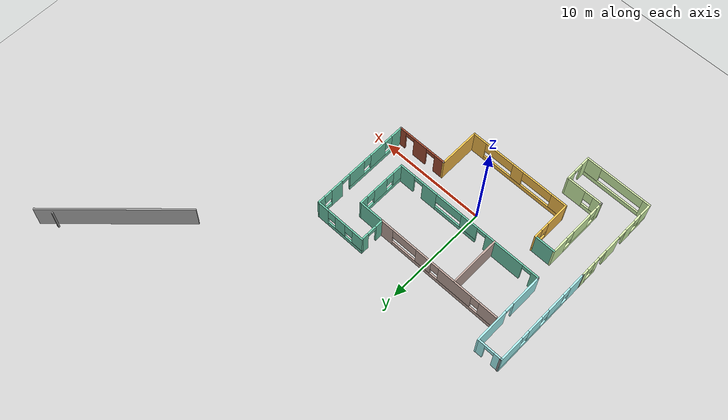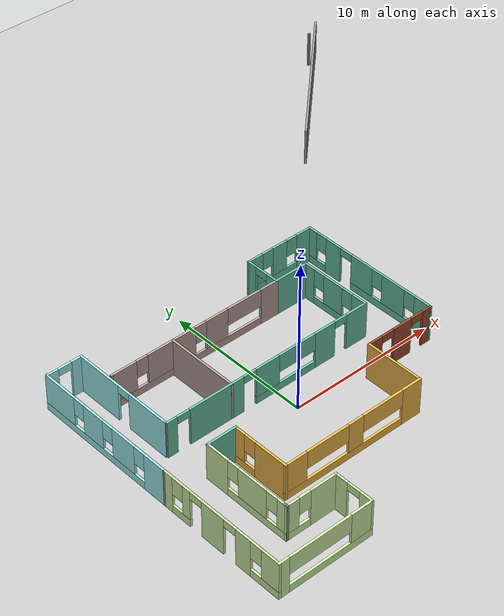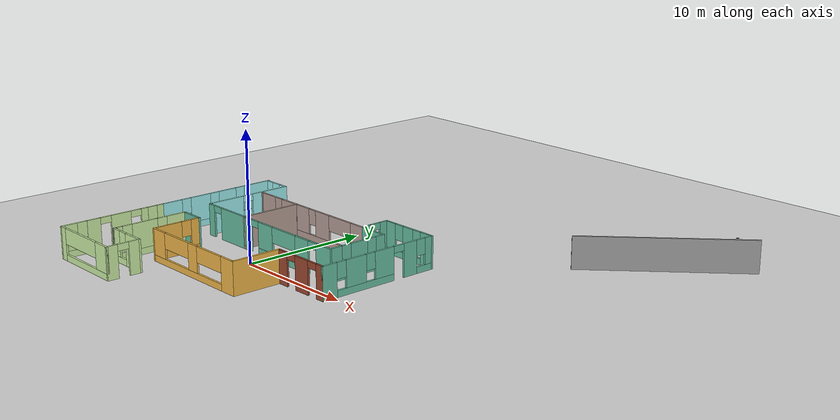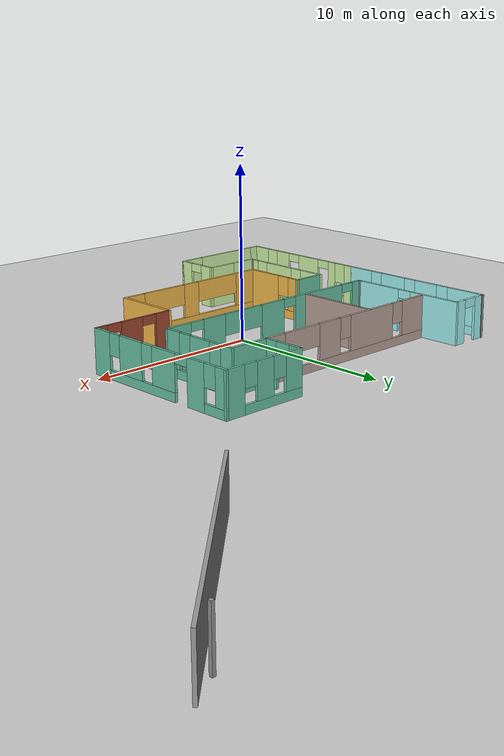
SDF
<sdf version="1.6">
 <world name="default">
  <plugin name="welcome" filename="libwelcome.so"/>
  <light name="sun" type="directional">
   <pose>0 0 10 0 -0 0</pose>
   <diffuse>0.8 0.8 0.8 1</diffuse>
   <specular>0.2 0.2 0.2 1</specular>
   <attenuation>
    <range>1000</range>
    <constant>0.9</constant>
    <linear>0.01</linear>
    <quadratic>0.001</quadratic>
   </attenuation>
   <direction>-0.5 0.1 -0.9</direction>
  </light>
  <model name="ground_plane">
   <static>1</static>
   <link name="link">
    <collision name="collision">
     <geometry><plane><normal>0 0 1</normal><size>100 100</size></plane></geometry>
     <surface>
      <contact><collide_bitmask>65535</collide_bitmask></contact>
      <friction><ode><mu>100</mu><mu2>50</mu2></ode></friction>
     </surface>
    </collision>
    <visual name="visual">
     <cast_shadows>0</cast_shadows>
     <geometry><plane><normal>0 0 1</normal><size>100 100</size></plane></geometry>
     <material>
      <script><uri>file://media/materials/scripts/gazebo.material</uri><name>Gazebo/Grey</name></script>
     </material>
    </visual>
   </link>
  </model>
  <gravity>0 0 -9.8</gravity>
  <magnetic_field>6e-06 2.3e-05 -4.2e-05</magnetic_field>
  <atmosphere type="adiabatic"/>
  <physics name="default_physics" default="0" type="ode">
   <max_step_size>0.001</max_step_size>
   <real_time_factor>1</real_time_factor>
   <real_time_update_rate>1000</real_time_update_rate>
  </physics>
  <scene><ambient>0.4 0.4 0.4 1</ambient><background>0.7 0.7 0.7 1</background><shadows>1</shadows></scene>
  <spherical_coordinates>
   <surface_model>EARTH_WGS84</surface_model>
   <latitude_deg>0</latitude_deg>
   <longitude_deg>0</longitude_deg>
   <elevation>0</elevation>
   <heading_deg>0</heading_deg>
  </spherical_coordinates>
  <model name="building">
   <pose>7.75122 8.09541 0 0 -0 0</pose>
   <link name="Wall_0">
    <pose>-8.08622 -12.7354 0 0 -0 3.14159</pose>
    <visual name="Wall_0_Visual_0">
     <pose>-4.28694 0 1.25 0 -0 0</pose>
     <geometry><box><size>1.42611 0.15 2.5</size></box></geometry>
     <material>
      <script><uri>file://media/materials/scripts/gazebo.material</uri><name>Gazebo/Grey</name></script>
      <ambient>1 0.764706 0.305882 1</ambient>
     </material>
     <meta><layer>0</layer></meta>
    </visual>
    <collision name="Wall_0_Collision_0">
     <geometry><box><size>1.42611 0.15 2.5</size></box></geometry>
     <pose>-4.28694 0 1.25 0 -0 0</pose>
    </collision>
    <visual name="Wall_0_Visual_1">
     <pose>0.713057 0 0.25 0 -0 0</pose>
     <geometry><box><size>8.57389 0.15 0.5</size></box></geometry>
     <material>
      <script><uri>file://media/materials/scripts/gazebo.material</uri><name>Gazebo/Grey</name></script>
      <ambient>1 0.764706 0.305882 1</ambient>
     </material>
     <meta><layer>0</layer></meta>
    </visual>
    <collision name="Wall_0_Collision_1">
     <geometry><box><size>8.57389 0.15 0.5</size></box></geometry>
     <pose>0.713057 0 0.25 0 -0 0</pose>
    </collision>
    <visual name="Wall_0_Visual_2">
     <pose>-0.101719 0 1.5 0 -0 0</pose>
     <geometry><box><size>1.08588 0.15 2</size></box></geometry>
     <material>
      <script><uri>file://media/materials/scripts/gazebo.material</uri><name>Gazebo/Grey</name></script>
      <ambient>1 0.764706 0.305882 1</ambient>
     </material>
     <meta><layer>0</layer></meta>
    </visual>
    <collision name="Wall_0_Collision_2">
     <geometry><box><size>1.08588 0.15 2</size></box></geometry>
     <pose>-0.101719 0 1.5 0 -0 0</pose>
    </collision>
    <visual name="Wall_0_Visual_3">
     <pose>4.22325 0 1.5 0 -0 0</pose>
     <geometry><box><size>1.55351 0.15 2</size></box></geometry>
     <material>
      <script><uri>file://media/materials/scripts/gazebo.material</uri><name>Gazebo/Grey</name></script>
      <ambient>1 0.764706 0.305882 1</ambient>
     </material>
     <meta><layer>0</layer></meta>
    </visual>
    <collision name="Wall_0_Collision_3">
     <geometry><box><size>1.55351 0.15 2</size></box></geometry>
     <pose>4.22325 0 1.5 0 -0 0</pose>
    </collision>
    <visual name="Wall_0_Visual_4">
     <pose>-2.10927 0 1.9 0 -0 0</pose>
     <geometry><box><size>2.92923 0.15 1.2</size></box></geometry>
     <material>
      <script><uri>file://media/materials/scripts/gazebo.material</uri><name>Gazebo/Grey</name></script>
      <ambient>1 0.764706 0.305882 1</ambient>
     </material>
     <meta><layer>0</layer></meta>
    </visual>
    <collision name="Wall_0_Collision_4">
     <geometry><box><size>2.92923 0.15 1.2</size></box></geometry>
     <pose>-2.10927 0 1.9 0 -0 0</pose>
    </collision>
    <visual name="Wall_0_Visual_5">
     <pose>1.94386 0 1.9 0 -0 0</pose>
     <geometry><box><size>3.00527 0.15 1.2</size></box></geometry>
     <material>
      <script><uri>file://media/materials/scripts/gazebo.material</uri><name>Gazebo/Grey</name></script>
      <ambient>1 0.764706 0.305882 1</ambient>
     </material>
     <meta><layer>0</layer></meta>
    </visual>
    <collision name="Wall_0_Collision_5">
     <geometry><box><size>3.00527 0.15 1.2</size></box></geometry>
     <pose>1.94386 0 1.9 0 -0 0</pose>
    </collision>
   </link>
   <link name="Wall_1">
    <pose>-13.0112 -10.8104 0 0 -0 1.5708</pose>
    <visual name="Wall_1_Visual_0">
     <pose>-0.814985 0 1.25 0 -0 0</pose>
     <geometry><box><size>2.37003 0.15 2.5</size></box></geometry>
     <material>
      <script><uri>file://media/materials/scripts/gazebo.material</uri><name>Gazebo/Grey</name></script>
      <ambient>1 0.764706 0.305882 1</ambient>
     </material>
     <meta><layer>0</layer></meta>
    </visual>
    <collision name="Wall_1_Collision_0">
     <geometry><box><size>2.37003 0.15 2.5</size></box></geometry>
     <pose>-0.814985 0 1.25 0 -0 0</pose>
    </collision>
    <visual name="Wall_1_Visual_1">
     <pose>1.18501 0 0.25 0 -0 0</pose>
     <geometry><box><size>1.62997 0.15 0.5</size></box></geometry>
     <material>
      <script><uri>file://media/materials/scripts/gazebo.material</uri><name>Gazebo/Grey</name></script>
      <ambient>1 0.764706 0.305882 1</ambient>
     </material>
     <meta><layer>0</layer></meta>
    </visual>
    <collision name="Wall_1_Collision_1">
     <geometry><box><size>1.62997 0.15 0.5</size></box></geometry>
     <pose>1.18501 0 0.25 0 -0 0</pose>
    </collision>
    <visual name="Wall_1_Visual_2">
     <pose>1.58502 0 1.5 0 -0 0</pose>
     <geometry><box><size>0.82997 0.15 2</size></box></geometry>
     <material>
      <script><uri>file://media/materials/scripts/gazebo.material</uri><name>Gazebo/Grey</name></script>
      <ambient>1 0.764706 0.305882 1</ambient>
     </material>
     <meta><layer>0</layer></meta>
    </visual>
    <collision name="Wall_1_Collision_2">
     <geometry><box><size>0.82997 0.15 2</size></box></geometry>
     <pose>1.58502 0 1.5 0 -0 0</pose>
    </collision>
    <visual name="Wall_1_Visual_3">
     <pose>0.77003 0 1.9 0 -0 0</pose>
     <geometry><box><size>0.8 0.15 1.2</size></box></geometry>
     <material>
      <script><uri>file://media/materials/scripts/gazebo.material</uri><name>Gazebo/Grey</name></script>
      <ambient>1 0.764706 0.305882 1</ambient>
     </material>
     <meta><layer>0</layer></meta>
    </visual>
    <collision name="Wall_1_Collision_3">
     <geometry><box><size>0.8 0.15 1.2</size></box></geometry>
     <pose>0.77003 0 1.9 0 -0 0</pose>
    </collision>
   </link>
   <link name="Wall_10">
    <collision name="Wall_10_Collision">
     <geometry><box><size>0.15 0.15 2.5</size></box></geometry>
     <pose>0 0 1.25 0 -0 0</pose>
    </collision>
    <visual name="Wall_10_Visual">
     <pose>0 0 1.25 0 -0 0</pose>
     <geometry><box><size>0.15 0.15 2.5</size></box></geometry>
     <material>
      <script><uri>file://media/materials/scripts/gazebo.material</uri><name>Gazebo/Grey</name></script>
      <ambient>1 1 1 1</ambient>
     </material>
     <meta><layer>0</layer></meta>
    </visual>
    <pose>-17.8612 -8.88541 0 0 -0 0</pose>
   </link>
   <link name="Wall_11">
    <collision name="Wall_11_Collision">
     <geometry><box><size>0.15 0.15 2.5</size></box></geometry>
     <pose>0 0 1.25 0 -0 0</pose>
    </collision>
    <visual name="Wall_11_Visual">
     <pose>0 0 1.25 0 -0 0</pose>
     <geometry><box><size>0.15 0.15 2.5</size></box></geometry>
     <material>
      <script><uri>file://media/materials/scripts/gazebo.material</uri><name>Gazebo/Grey</name></script>
      <ambient>1 1 1 1</ambient>
     </material>
     <meta><layer>0</layer></meta>
    </visual>
    <pose>-17.8612 -8.88541 0 0 -0 0</pose>
   </link>
   <link name="Wall_13">
    <collision name="Wall_13_Collision">
     <geometry><box><size>0.15 0.15 2.5</size></box></geometry>
     <pose>0 0 1.25 0 -0 0</pose>
    </collision>
    <visual name="Wall_13_Visual">
     <pose>0 0 1.25 0 -0 0</pose>
     <geometry><box><size>0.15 0.15 2.5</size></box></geometry>
     <material>
      <script><uri>file://media/materials/scripts/gazebo.material</uri><name>Gazebo/Grey</name></script>
      <ambient>1 1 1 1</ambient>
     </material>
     <meta><layer>0</layer></meta>
    </visual>
    <pose>-17.8612 -8.88541 0 0 -0 0</pose>
   </link>
   <link name="Wall_16">
    <collision name="Wall_16_Collision">
     <geometry><box><size>0.15 0.15 2.5</size></box></geometry>
     <pose>0 0 1.25 0 -0 0</pose>
    </collision>
    <visual name="Wall_16_Visual">
     <pose>0 0 1.25 0 -0 0</pose>
     <geometry><box><size>0.15 0.15 2.5</size></box></geometry>
     <material>
      <script><uri>file://media/materials/scripts/gazebo.material</uri><name>Gazebo/Grey</name></script>
      <ambient>1 1 1 1</ambient>
     </material>
     <meta><layer>0</layer></meta>
    </visual>
    <pose>-17.7916 1.00147 0 0 -0 0</pose>
   </link>
   <link name="Wall_19">
    <collision name="Wall_19_Collision">
     <geometry><box><size>13.2246 0.15 2.5</size></box></geometry>
     <pose>0 0 1.25 0 -0 0</pose>
    </collision>
    <visual name="Wall_19_Visual">
     <pose>0 0 1.25 0 -0 0</pose>
     <geometry><box><size>13.2246 0.15 2.5</size></box></geometry>
     <material>
      <script><uri>file://media/materials/scripts/gazebo.material</uri><name>Gazebo/Grey</name></script>
      <ambient>1 1 1 1</ambient>
     </material>
     <meta><layer>0</layer></meta>
    </visual>
    <pose>13.1096 12.9319 0 0 0 -2.37763</pose>
   </link>
   <link name="Wall_20">
    <collision name="Wall_20_Collision">
     <geometry><box><size>0.15 0.15 2.5</size></box></geometry>
     <pose>0 0 1.25 0 -0 0</pose>
    </collision>
    <visual name="Wall_20_Visual">
     <pose>0 0 1.25 0 -0 0</pose>
     <geometry><box><size>0.15 0.15 2.5</size></box></geometry>
     <material>
      <script><uri>file://media/materials/scripts/gazebo.material</uri><name>Gazebo/Grey</name></script>
      <ambient>1 1 1 1</ambient>
     </material>
     <meta><layer>0</layer></meta>
    </visual>
    <pose>16.475 16.6544 0 0 -0 0</pose>
   </link>
   <link name="Wall_22">
    <pose>1.65837 -3.96041 0 0 -0 1.5708</pose>
    <visual name="Wall_22_Visual_0">
     <pose>-4.3788 0 1.25 0 -0 0</pose>
     <geometry><box><size>1.2424 0.15 2.5</size></box></geometry>
     <material>
      <script><uri>file://media/materials/scripts/gazebo.material</uri><name>Gazebo/Grey</name></script>
      <ambient>0.435294 0.796078 0.67451 1</ambient>
     </material>
     <meta><layer>0</layer></meta>
    </visual>
    <collision name="Wall_22_Collision_0">
     <geometry><box><size>1.2424 0.15 2.5</size></box></geometry>
     <pose>-4.3788 0 1.25 0 -0 0</pose>
    </collision>
    <visual name="Wall_22_Visual_1">
     <pose>2.84528 0 1.25 0 -0 0</pose>
     <geometry><box><size>1.21212 0.15 2.5</size></box></geometry>
     <material>
      <script><uri>file://media/materials/scripts/gazebo.material</uri><name>Gazebo/Grey</name></script>
      <ambient>0.435294 0.796078 0.67451 1</ambient>
     </material>
     <meta><layer>0</layer></meta>
    </visual>
    <collision name="Wall_22_Collision_1">
     <geometry><box><size>1.21212 0.15 2.5</size></box></geometry>
     <pose>2.84528 0 1.25 0 -0 0</pose>
    </collision>
    <visual name="Wall_22_Visual_2">
     <pose>-1.20919 0 0.25 0 -0 0</pose>
     <geometry><box><size>5.09682 0.15 0.5</size></box></geometry>
     <material>
      <script><uri>file://media/materials/scripts/gazebo.material</uri><name>Gazebo/Grey</name></script>
      <ambient>0.435294 0.796078 0.67451 1</ambient>
     </material>
     <meta><layer>0</layer></meta>
    </visual>
    <collision name="Wall_22_Collision_2">
     <geometry><box><size>5.09682 0.15 0.5</size></box></geometry>
     <pose>-1.20919 0 0.25 0 -0 0</pose>
    </collision>
    <visual name="Wall_22_Visual_3">
     <pose>4.22567 0 0.25 0 -0 0</pose>
     <geometry><box><size>1.54866 0.15 0.5</size></box></geometry>
     <material>
      <script><uri>file://media/materials/scripts/gazebo.material</uri><name>Gazebo/Grey</name></script>
      <ambient>0.435294 0.796078 0.67451 1</ambient>
     </material>
     <meta><layer>0</layer></meta>
    </visual>
    <collision name="Wall_22_Collision_3">
     <geometry><box><size>1.54866 0.15 0.5</size></box></geometry>
     <pose>4.22567 0 0.25 0 -0 0</pose>
    </collision>
    <visual name="Wall_22_Visual_4">
     <pose>-2.07246 0 1.5 0 -0 0</pose>
     <geometry><box><size>1.77028 0.15 2</size></box></geometry>
     <material>
      <script><uri>file://media/materials/scripts/gazebo.material</uri><name>Gazebo/Grey</name></script>
      <ambient>0.435294 0.796078 0.67451 1</ambient>
     </material>
     <meta><layer>0</layer></meta>
    </visual>
    <collision name="Wall_22_Collision_4">
     <geometry><box><size>1.77028 0.15 2</size></box></geometry>
     <pose>-2.07246 0 1.5 0 -0 0</pose>
    </collision>
    <visual name="Wall_22_Visual_5">
     <pose>0.475947 0 1.5 0 -0 0</pose>
     <geometry><box><size>1.72654 0.15 2</size></box></geometry>
     <material>
      <script><uri>file://media/materials/scripts/gazebo.material</uri><name>Gazebo/Grey</name></script>
      <ambient>0.435294 0.796078 0.67451 1</ambient>
     </material>
     <meta><layer>0</layer></meta>
    </visual>
    <collision name="Wall_22_Collision_5">
     <geometry><box><size>1.72654 0.15 2</size></box></geometry>
     <pose>0.475947 0 1.5 0 -0 0</pose>
    </collision>
    <visual name="Wall_22_Visual_6">
     <pose>0.475947 0 1.5 0 -0 0</pose>
     <geometry><box><size>1.72654 0.15 2</size></box></geometry>
     <material>
      <script><uri>file://media/materials/scripts/gazebo.material</uri><name>Gazebo/Grey</name></script>
      <ambient>0.435294 0.796078 0.67451 1</ambient>
     </material>
     <meta><layer>0</layer></meta>
    </visual>
    <collision name="Wall_22_Collision_6">
     <geometry><box><size>1.72654 0.15 2</size></box></geometry>
     <pose>0.475947 0 1.5 0 -0 0</pose>
    </collision>
    <visual name="Wall_22_Visual_7">
     <pose>4.62567 0 1.5 0 -0 0</pose>
     <geometry><box><size>0.748656 0.15 2</size></box></geometry>
     <material>
      <script><uri>file://media/materials/scripts/gazebo.material</uri><name>Gazebo/Grey</name></script>
      <ambient>0.435294 0.796078 0.67451 1</ambient>
     </material>
     <meta><layer>0</layer></meta>
    </visual>
    <collision name="Wall_22_Collision_7">
     <geometry><box><size>0.748656 0.15 2</size></box></geometry>
     <pose>4.62567 0 1.5 0 -0 0</pose>
    </collision>
    <visual name="Wall_22_Visual_8">
     <pose>-3.3576 0 1.9 0 -0 0</pose>
     <geometry><box><size>0.8 0.15 1.2</size></box></geometry>
     <material>
      <script><uri>file://media/materials/scripts/gazebo.material</uri><name>Gazebo/Grey</name></script>
      <ambient>0.435294 0.796078 0.67451 1</ambient>
     </material>
     <meta><layer>0</layer></meta>
    </visual>
    <collision name="Wall_22_Collision_8">
     <geometry><box><size>0.8 0.15 1.2</size></box></geometry>
     <pose>-3.3576 0 1.9 0 -0 0</pose>
    </collision>
    <visual name="Wall_22_Visual_9">
     <pose>3.85134 0 1.9 0 -0 0</pose>
     <geometry><box><size>0.8 0.15 1.2</size></box></geometry>
     <material>
      <script><uri>file://media/materials/scripts/gazebo.material</uri><name>Gazebo/Grey</name></script>
      <ambient>0.435294 0.796078 0.67451 1</ambient>
     </material>
     <meta><layer>0</layer></meta>
    </visual>
    <collision name="Wall_22_Collision_9">
     <geometry><box><size>0.8 0.15 1.2</size></box></geometry>
     <pose>3.85134 0 1.9 0 -0 0</pose>
    </collision>
    <visual name="Wall_22_Visual_10">
     <pose>-0.787325 0 1.9 0 -0 0</pose>
     <geometry><box><size>0.8 0.15 1.2</size></box></geometry>
     <material>
      <script><uri>file://media/materials/scripts/gazebo.material</uri><name>Gazebo/Grey</name></script>
      <ambient>0.435294 0.796078 0.67451 1</ambient>
     </material>
     <meta><layer>0</layer></meta>
    </visual>
    <collision name="Wall_22_Collision_10">
     <geometry><box><size>0.8 0.15 1.2</size></box></geometry>
     <pose>-0.787325 0 1.9 0 -0 0</pose>
    </collision>
    <visual name="Wall_22_Visual_11">
     <pose>1.78922 0 2.25 0 -0 0</pose>
     <geometry><box><size>0.9 0.15 0.5</size></box></geometry>
     <material>
      <script><uri>file://media/materials/scripts/gazebo.material</uri><name>Gazebo/Grey</name></script>
      <ambient>0.435294 0.796078 0.67451 1</ambient>
     </material>
     <meta><layer>0</layer></meta>
    </visual>
    <collision name="Wall_22_Collision_11">
     <geometry><box><size>0.9 0.15 0.5</size></box></geometry>
     <pose>1.78922 0 2.25 0 -0 0</pose>
    </collision>
    <visual name="Wall_22_Visual_12">
     <pose>1.78922 0 2.25 0 -0 0</pose>
     <geometry><box><size>0.9 0.15 0.5</size></box></geometry>
     <material>
      <script><uri>file://media/materials/scripts/gazebo.material</uri><name>Gazebo/Grey</name></script>
      <ambient>0.435294 0.796078 0.67451 1</ambient>
     </material>
     <meta><layer>0</layer></meta>
    </visual>
    <collision name="Wall_22_Collision_12">
     <geometry><box><size>0.9 0.15 0.5</size></box></geometry>
     <pose>1.78922 0 2.25 0 -0 0</pose>
    </collision>
   </link>
   <link name="Wall_23">
    <pose>-0.766634 0.964587 0 0 -0 3.14159</pose>
    <visual name="Wall_23_Visual_0">
     <pose>-1.90941 0 1.25 0 -0 0</pose>
     <geometry><box><size>1.18118 0.15 2.5</size></box></geometry>
     <material>
      <script><uri>file://media/materials/scripts/gazebo.material</uri><name>Gazebo/Grey</name></script>
      <ambient>0.435294 0.796078 0.67451 1</ambient>
     </material>
     <meta><layer>0</layer></meta>
    </visual>
    <collision name="Wall_23_Collision_0">
     <geometry><box><size>1.18118 0.15 2.5</size></box></geometry>
     <pose>-1.90941 0 1.25 0 -0 0</pose>
    </collision>
    <visual name="Wall_23_Visual_1">
     <pose>0.590591 0 0.25 0 -0 0</pose>
     <geometry><box><size>3.81882 0.15 0.5</size></box></geometry>
     <material>
      <script><uri>file://media/materials/scripts/gazebo.material</uri><name>Gazebo/Grey</name></script>
      <ambient>0.435294 0.796078 0.67451 1</ambient>
     </material>
     <meta><layer>0</layer></meta>
    </visual>
    <collision name="Wall_23_Collision_1">
     <geometry><box><size>3.81882 0.15 0.5</size></box></geometry>
     <pose>0.590591 0 0.25 0 -0 0</pose>
    </collision>
    <visual name="Wall_23_Visual_2">
     <pose>0.031729 0 1.5 0 -0 0</pose>
     <geometry><box><size>1.10109 0.15 2</size></box></geometry>
     <material>
      <script><uri>file://media/materials/scripts/gazebo.material</uri><name>Gazebo/Grey</name></script>
      <ambient>0.435294 0.796078 0.67451 1</ambient>
     </material>
     <meta><layer>0</layer></meta>
    </visual>
    <collision name="Wall_23_Collision_2">
     <geometry><box><size>1.10109 0.15 2</size></box></geometry>
     <pose>0.031729 0 1.5 0 -0 0</pose>
    </collision>
    <visual name="Wall_23_Visual_3">
     <pose>1.94114 0 1.5 0 -0 0</pose>
     <geometry><box><size>1.11772 0.15 2</size></box></geometry>
     <material>
      <script><uri>file://media/materials/scripts/gazebo.material</uri><name>Gazebo/Grey</name></script>
      <ambient>0.435294 0.796078 0.67451 1</ambient>
     </material>
     <meta><layer>0</layer></meta>
    </visual>
    <collision name="Wall_23_Collision_3">
     <geometry><box><size>1.11772 0.15 2</size></box></geometry>
     <pose>1.94114 0 1.5 0 -0 0</pose>
    </collision>
    <visual name="Wall_23_Visual_4">
     <pose>-0.918818 0 1.9 0 -0 0</pose>
     <geometry><box><size>0.8 0.15 1.2</size></box></geometry>
     <material>
      <script><uri>file://media/materials/scripts/gazebo.material</uri><name>Gazebo/Grey</name></script>
      <ambient>0.435294 0.796078 0.67451 1</ambient>
     </material>
     <meta><layer>0</layer></meta>
    </visual>
    <collision name="Wall_23_Collision_4">
     <geometry><box><size>0.8 0.15 1.2</size></box></geometry>
     <pose>-0.918818 0 1.9 0 -0 0</pose>
    </collision>
    <visual name="Wall_23_Visual_5">
     <pose>0.982276 0 1.9 0 -0 0</pose>
     <geometry><box><size>0.8 0.15 1.2</size></box></geometry>
     <material>
      <script><uri>file://media/materials/scripts/gazebo.material</uri><name>Gazebo/Grey</name></script>
      <ambient>0.435294 0.796078 0.67451 1</ambient>
     </material>
     <meta><layer>0</layer></meta>
    </visual>
    <collision name="Wall_23_Collision_5">
     <geometry><box><size>0.8 0.15 1.2</size></box></geometry>
     <pose>0.982276 0 1.9 0 -0 0</pose>
    </collision>
   </link>
   <link name="Wall_24">
    <pose>-3.19163 -0.210413 0 0 0 -1.5708</pose>
    <visual name="Wall_24_Visual_0">
     <pose>-0.870254 0 1.25 0 -0 0</pose>
     <geometry><box><size>0.759491 0.15 2.5</size></box></geometry>
     <material>
      <script><uri>file://media/materials/scripts/gazebo.material</uri><name>Gazebo/Grey</name></script>
      <ambient>0.435294 0.796078 0.67451 1</ambient>
     </material>
     <meta><layer>0</layer></meta>
    </visual>
    <collision name="Wall_24_Collision_0">
     <geometry><box><size>0.759491 0.15 2.5</size></box></geometry>
     <pose>-0.870254 0 1.25 0 -0 0</pose>
    </collision>
    <visual name="Wall_24_Visual_1">
     <pose>0.829746 0 1.25 0 -0 0</pose>
     <geometry><box><size>0.840509 0.15 2.5</size></box></geometry>
     <material>
      <script><uri>file://media/materials/scripts/gazebo.material</uri><name>Gazebo/Grey</name></script>
      <ambient>0.435294 0.796078 0.67451 1</ambient>
     </material>
     <meta><layer>0</layer></meta>
    </visual>
    <collision name="Wall_24_Collision_1">
     <geometry><box><size>0.840509 0.15 2.5</size></box></geometry>
     <pose>0.829746 0 1.25 0 -0 0</pose>
    </collision>
    <visual name="Wall_24_Visual_2">
     <pose>-0.040509 0 2.25 0 -0 0</pose>
     <geometry><box><size>0.9 0.15 0.5</size></box></geometry>
     <material>
      <script><uri>file://media/materials/scripts/gazebo.material</uri><name>Gazebo/Grey</name></script>
      <ambient>0.435294 0.796078 0.67451 1</ambient>
     </material>
     <meta><layer>0</layer></meta>
    </visual>
    <collision name="Wall_24_Collision_2">
     <geometry><box><size>0.9 0.15 0.5</size></box></geometry>
     <pose>-0.040509 0 2.25 0 -0 0</pose>
    </collision>
   </link>
   <link name="Wall_25">
    <collision name="Wall_25_Collision">
     <geometry><box><size>2.5 0.15 2.5</size></box></geometry>
     <pose>0 0 1.25 0 -0 0</pose>
    </collision>
    <visual name="Wall_25_Visual">
     <pose>0 0 1.25 0 -0 0</pose>
     <geometry><box><size>2.5 0.15 2.5</size></box></geometry>
     <material>
      <script><uri>file://media/materials/scripts/gazebo.material</uri><name>Gazebo/Grey</name></script>
      <ambient>0.435294 0.796078 0.67451 1</ambient>
     </material>
     <meta><layer>0</layer></meta>
    </visual>
    <pose>-2.01663 -1.38541 0 0 -0 0</pose>
   </link>
   <link name="Wall_26">
    <pose>-0.841634 -3.81041 0 0 0 -1.5708</pose>
    <visual name="Wall_26_Visual_0">
     <pose>-2.09158 0 1.25 0 -0 0</pose>
     <geometry><box><size>0.816847 0.15 2.5</size></box></geometry>
     <material>
      <script><uri>file://media/materials/scripts/gazebo.material</uri><name>Gazebo/Grey</name></script>
      <ambient>0.435294 0.796078 0.67451 1</ambient>
     </material>
     <meta><layer>0</layer></meta>
    </visual>
    <collision name="Wall_26_Collision_0">
     <geometry><box><size>0.816847 0.15 2.5</size></box></geometry>
     <pose>-2.09158 0 1.25 0 -0 0</pose>
    </collision>
    <visual name="Wall_26_Visual_1">
     <pose>0.408424 0 0.25 0 -0 0</pose>
     <geometry><box><size>4.18315 0.15 0.5</size></box></geometry>
     <material>
      <script><uri>file://media/materials/scripts/gazebo.material</uri><name>Gazebo/Grey</name></script>
      <ambient>0.435294 0.796078 0.67451 1</ambient>
     </material>
     <meta><layer>0</layer></meta>
    </visual>
    <collision name="Wall_26_Collision_1">
     <geometry><box><size>4.18315 0.15 0.5</size></box></geometry>
     <pose>0.408424 0 0.25 0 -0 0</pose>
    </collision>
    <visual name="Wall_26_Visual_2">
     <pose>-0.134892 0 1.5 0 -0 0</pose>
     <geometry><box><size>1.49652 0.15 2</size></box></geometry>
     <material>
      <script><uri>file://media/materials/scripts/gazebo.material</uri><name>Gazebo/Grey</name></script>
      <ambient>0.435294 0.796078 0.67451 1</ambient>
     </material>
     <meta><layer>0</layer></meta>
    </visual>
    <collision name="Wall_26_Collision_2">
     <geometry><box><size>1.49652 0.15 2</size></box></geometry>
     <pose>-0.134892 0 1.5 0 -0 0</pose>
    </collision>
    <visual name="Wall_26_Visual_3">
     <pose>1.95668 0 1.5 0 -0 0</pose>
     <geometry><box><size>1.08663 0.15 2</size></box></geometry>
     <material>
      <script><uri>file://media/materials/scripts/gazebo.material</uri><name>Gazebo/Grey</name></script>
      <ambient>0.435294 0.796078 0.67451 1</ambient>
     </material>
     <meta><layer>0</layer></meta>
    </visual>
    <collision name="Wall_26_Collision_3">
     <geometry><box><size>1.08663 0.15 2</size></box></geometry>
     <pose>1.95668 0 1.5 0 -0 0</pose>
    </collision>
    <visual name="Wall_26_Visual_4">
     <pose>-1.28315 0 1.9 0 -0 0</pose>
     <geometry><box><size>0.8 0.15 1.2</size></box></geometry>
     <material>
      <script><uri>file://media/materials/scripts/gazebo.material</uri><name>Gazebo/Grey</name></script>
      <ambient>0.435294 0.796078 0.67451 1</ambient>
     </material>
     <meta><layer>0</layer></meta>
    </visual>
    <collision name="Wall_26_Collision_4">
     <geometry><box><size>0.8 0.15 1.2</size></box></geometry>
     <pose>-1.28315 0 1.9 0 -0 0</pose>
    </collision>
    <visual name="Wall_26_Visual_5">
     <pose>1.01337 0 1.9 0 -0 0</pose>
     <geometry><box><size>0.8 0.15 1.2</size></box></geometry>
     <material>
      <script><uri>file://media/materials/scripts/gazebo.material</uri><name>Gazebo/Grey</name></script>
      <ambient>0.435294 0.796078 0.67451 1</ambient>
     </material>
     <meta><layer>0</layer></meta>
    </visual>
    <collision name="Wall_26_Collision_5">
     <geometry><box><size>0.8 0.15 1.2</size></box></geometry>
     <pose>1.01337 0 1.9 0 -0 0</pose>
    </collision>
   </link>
   <link name="Wall_27">
    <pose>-8.14163 -6.23541 0 0 -0 3.14159</pose>
    <visual name="Wall_27_Visual_0">
     <pose>-6.57656 0 1.25 0 -0 0</pose>
     <geometry><box><size>1.59689 0.15 2.5</size></box></geometry>
     <material>
      <script><uri>file://media/materials/scripts/gazebo.material</uri><name>Gazebo/Grey</name></script>
      <ambient>0.435294 0.796078 0.67451 1</ambient>
     </material>
     <meta><layer>0</layer></meta>
    </visual>
    <collision name="Wall_27_Collision_0">
     <geometry><box><size>1.59689 0.15 2.5</size></box></geometry>
     <pose>-6.57656 0 1.25 0 -0 0</pose>
    </collision>
    <visual name="Wall_27_Visual_1">
     <pose>-4.12443 0 1.25 0 -0 0</pose>
     <geometry><box><size>1.50736 0.15 2.5</size></box></geometry>
     <material>
      <script><uri>file://media/materials/scripts/gazebo.material</uri><name>Gazebo/Grey</name></script>
      <ambient>0.435294 0.796078 0.67451 1</ambient>
     </material>
     <meta><layer>0</layer></meta>
    </visual>
    <collision name="Wall_27_Collision_1">
     <geometry><box><size>1.50736 0.15 2.5</size></box></geometry>
     <pose>-4.12443 0 1.25 0 -0 0</pose>
    </collision>
    <visual name="Wall_27_Visual_2">
     <pose>3.86558 0 1.25 0 -0 0</pose>
     <geometry><box><size>3.82992 0.15 2.5</size></box></geometry>
     <material>
      <script><uri>file://media/materials/scripts/gazebo.material</uri><name>Gazebo/Grey</name></script>
      <ambient>0.435294 0.796078 0.67451 1</ambient>
     </material>
     <meta><layer>0</layer></meta>
    </visual>
    <collision name="Wall_27_Collision_2">
     <geometry><box><size>3.82992 0.15 2.5</size></box></geometry>
     <pose>3.86558 0 1.25 0 -0 0</pose>
    </collision>
    <visual name="Wall_27_Visual_3">
     <pose>7.02777 0 1.25 0 -0 0</pose>
     <geometry><box><size>0.694461 0.15 2.5</size></box></geometry>
     <material>
      <script><uri>file://media/materials/scripts/gazebo.material</uri><name>Gazebo/Grey</name></script>
      <ambient>0.435294 0.796078 0.67451 1</ambient>
     </material>
     <meta><layer>0</layer></meta>
    </visual>
    <collision name="Wall_27_Collision_3">
     <geometry><box><size>0.694461 0.15 2.5</size></box></geometry>
     <pose>7.02777 0 1.25 0 -0 0</pose>
    </collision>
    <visual name="Wall_27_Visual_4">
     <pose>-1.16007 0 0.25 0 -0 0</pose>
     <geometry><box><size>4.42137 0.15 0.5</size></box></geometry>
     <material>
      <script><uri>file://media/materials/scripts/gazebo.material</uri><name>Gazebo/Grey</name></script>
      <ambient>0.435294 0.796078 0.67451 1</ambient>
     </material>
     <meta><layer>0</layer></meta>
    </visual>
    <collision name="Wall_27_Collision_4">
     <geometry><box><size>4.42137 0.15 0.5</size></box></geometry>
     <pose>-1.16007 0 0.25 0 -0 0</pose>
    </collision>
    <visual name="Wall_27_Visual_5">
     <pose>0.198082 0 1.5 0 -0 0</pose>
     <geometry><box><size>1.70507 0.15 2</size></box></geometry>
     <material>
      <script><uri>file://media/materials/scripts/gazebo.material</uri><name>Gazebo/Grey</name></script>
      <ambient>0.435294 0.796078 0.67451 1</ambient>
     </material>
     <meta><layer>0</layer></meta>
    </visual>
    <collision name="Wall_27_Collision_5">
     <geometry><box><size>1.70507 0.15 2</size></box></geometry>
     <pose>0.198082 0 1.5 0 -0 0</pose>
    </collision>
    <visual name="Wall_27_Visual_6">
     <pose>-2.0126 0 1.9 0 -0 0</pose>
     <geometry><box><size>2.7163 0.15 1.2</size></box></geometry>
     <material>
      <script><uri>file://media/materials/scripts/gazebo.material</uri><name>Gazebo/Grey</name></script>
      <ambient>0.435294 0.796078 0.67451 1</ambient>
     </material>
     <meta><layer>0</layer></meta>
    </visual>
    <collision name="Wall_27_Collision_6">
     <geometry><box><size>2.7163 0.15 1.2</size></box></geometry>
     <pose>-2.0126 0 1.9 0 -0 0</pose>
    </collision>
    <visual name="Wall_27_Visual_7">
     <pose>-5.32811 0 2.25 0 -0 0</pose>
     <geometry><box><size>0.9 0.15 0.5</size></box></geometry>
     <material>
      <script><uri>file://media/materials/scripts/gazebo.material</uri><name>Gazebo/Grey</name></script>
      <ambient>0.435294 0.796078 0.67451 1</ambient>
     </material>
     <meta><layer>0</layer></meta>
    </visual>
    <collision name="Wall_27_Collision_7">
     <geometry><box><size>0.9 0.15 0.5</size></box></geometry>
     <pose>-5.32811 0 2.25 0 -0 0</pose>
    </collision>
    <visual name="Wall_27_Visual_8">
     <pose>6.23054 0 2.25 0 -0 0</pose>
     <geometry><box><size>0.9 0.15 0.5</size></box></geometry>
     <material>
      <script><uri>file://media/materials/scripts/gazebo.material</uri><name>Gazebo/Grey</name></script>
      <ambient>0.435294 0.796078 0.67451 1</ambient>
     </material>
     <meta><layer>0</layer></meta>
    </visual>
    <collision name="Wall_27_Collision_8">
     <geometry><box><size>0.9 0.15 0.5</size></box></geometry>
     <pose>6.23054 0 2.25 0 -0 0</pose>
    </collision>
    <visual name="Wall_27_Visual_9">
     <pose>1.50062 0 2.25 0 -0 0</pose>
     <geometry><box><size>0.9 0.15 0.5</size></box></geometry>
     <material>
      <script><uri>file://media/materials/scripts/gazebo.material</uri><name>Gazebo/Grey</name></script>
      <ambient>0.435294 0.796078 0.67451 1</ambient>
     </material>
     <meta><layer>0</layer></meta>
    </visual>
    <collision name="Wall_27_Collision_9">
     <geometry><box><size>0.9 0.15 0.5</size></box></geometry>
     <pose>1.50062 0 2.25 0 -0 0</pose>
    </collision>
   </link>
   <link name="Wall_3">
    <collision name="Wall_3_Collision">
     <geometry><box><size>4 0.15 2.5</size></box></geometry>
     <pose>0 0 1.25 0 -0 0</pose>
    </collision>
    <visual name="Wall_3_Visual">
     <pose>0 0 1.25 0 -0 0</pose>
     <geometry><box><size>4 0.15 2.5</size></box></geometry>
     <material>
      <script><uri>file://media/materials/scripts/gazebo.material</uri><name>Gazebo/Grey</name></script>
      <ambient>1 0.764706 0.305882 1</ambient>
     </material>
     <meta><layer>0</layer></meta>
    </visual>
    <pose>-3.16122 -10.8104 0 0 -0 1.5708</pose>
   </link>
   <link name="Wall_30">
    <collision name="Wall_30_Collision">
     <geometry><box><size>0.15 0.15 2.5</size></box></geometry>
     <pose>0 0 1.25 0 -0 0</pose>
    </collision>
    <visual name="Wall_30_Visual">
     <pose>0 0 1.25 0 -0 0</pose>
     <geometry><box><size>0.15 0.15 2.5</size></box></geometry>
     <material>
      <script><uri>file://media/materials/scripts/gazebo.material</uri><name>Gazebo/Grey</name></script>
      <ambient>1 1 1 1</ambient>
     </material>
     <meta><layer>0</layer></meta>
    </visual>
    <pose>-17.7916 1.00147 0 0 -0 0</pose>
   </link>
   <link name="Wall_32">
    <pose>-17.8612 -3.96041 0 0 -0 1.5708</pose>
    <visual name="Wall_32_Visual_0">
     <pose>-4.15067 0 1.25 0 -0 0</pose>
     <geometry><box><size>1.69866 0.15 2.5</size></box></geometry>
     <material>
      <script><uri>file://media/materials/scripts/gazebo.material</uri><name>Gazebo/Grey</name></script>
      <ambient>0.666667 1 1 1</ambient>
     </material>
     <meta><layer>0</layer></meta>
    </visual>
    <collision name="Wall_32_Collision_0">
     <geometry><box><size>1.69866 0.15 2.5</size></box></geometry>
     <pose>-4.15067 0 1.25 0 -0 0</pose>
    </collision>
    <visual name="Wall_32_Visual_1">
     <pose>0.849329 0 0.25 0 -0 0</pose>
     <geometry><box><size>8.30134 0.15 0.5</size></box></geometry>
     <material>
      <script><uri>file://media/materials/scripts/gazebo.material</uri><name>Gazebo/Grey</name></script>
      <ambient>0.666667 1 1 1</ambient>
     </material>
     <meta><layer>0</layer></meta>
    </visual>
    <collision name="Wall_32_Collision_1">
     <geometry><box><size>8.30134 0.15 0.5</size></box></geometry>
     <pose>0.849329 0 0.25 0 -0 0</pose>
    </collision>
    <visual name="Wall_32_Visual_2">
     <pose>-1.60099 0 1.5 0 -0 0</pose>
     <geometry><box><size>1.8007 0.15 2</size></box></geometry>
     <material>
      <script><uri>file://media/materials/scripts/gazebo.material</uri><name>Gazebo/Grey</name></script>
      <ambient>0.666667 1 1 1</ambient>
     </material>
     <meta><layer>0</layer></meta>
    </visual>
    <collision name="Wall_32_Collision_2">
     <geometry><box><size>1.8007 0.15 2</size></box></geometry>
     <pose>-1.60099 0 1.5 0 -0 0</pose>
    </collision>
    <visual name="Wall_32_Visual_3">
     <pose>0.90845 0 1.5 0 -0 0</pose>
     <geometry><box><size>1.61819 0.15 2</size></box></geometry>
     <material>
      <script><uri>file://media/materials/scripts/gazebo.material</uri><name>Gazebo/Grey</name></script>
      <ambient>0.666667 1 1 1</ambient>
     </material>
     <meta><layer>0</layer></meta>
    </visual>
    <collision name="Wall_32_Collision_3">
     <geometry><box><size>1.61819 0.15 2</size></box></geometry>
     <pose>0.90845 0 1.5 0 -0 0</pose>
    </collision>
    <visual name="Wall_32_Visual_4">
     <pose>3.75877 0 1.5 0 -0 0</pose>
     <geometry><box><size>2.48245 0.15 2</size></box></geometry>
     <material>
      <script><uri>file://media/materials/scripts/gazebo.material</uri><name>Gazebo/Grey</name></script>
      <ambient>0.666667 1 1 1</ambient>
     </material>
     <meta><layer>0</layer></meta>
    </visual>
    <collision name="Wall_32_Collision_4">
     <geometry><box><size>2.48245 0.15 2</size></box></geometry>
     <pose>3.75877 0 1.5 0 -0 0</pose>
    </collision>
    <visual name="Wall_32_Visual_5">
     <pose>-2.90134 0 1.9 0 -0 0</pose>
     <geometry><box><size>0.8 0.15 1.2</size></box></geometry>
     <material>
      <script><uri>file://media/materials/scripts/gazebo.material</uri><name>Gazebo/Grey</name></script>
      <ambient>0.666667 1 1 1</ambient>
     </material>
     <meta><layer>0</layer></meta>
    </visual>
    <collision name="Wall_32_Collision_5">
     <geometry><box><size>0.8 0.15 1.2</size></box></geometry>
     <pose>-2.90134 0 1.9 0 -0 0</pose>
    </collision>
    <visual name="Wall_32_Visual_6">
     <pose>-0.300645 0 1.9 0 -0 0</pose>
     <geometry><box><size>0.8 0.15 1.2</size></box></geometry>
     <material>
      <script><uri>file://media/materials/scripts/gazebo.material</uri><name>Gazebo/Grey</name></script>
      <ambient>0.666667 1 1 1</ambient>
     </material>
     <meta><layer>0</layer></meta>
    </visual>
    <collision name="Wall_32_Collision_6">
     <geometry><box><size>0.8 0.15 1.2</size></box></geometry>
     <pose>-0.300645 0 1.9 0 -0 0</pose>
    </collision>
    <visual name="Wall_32_Visual_7">
     <pose>2.11755 0 1.9 0 -0 0</pose>
     <geometry><box><size>0.8 0.15 1.2</size></box></geometry>
     <material>
      <script><uri>file://media/materials/scripts/gazebo.material</uri><name>Gazebo/Grey</name></script>
      <ambient>0.666667 1 1 1</ambient>
     </material>
     <meta><layer>0</layer></meta>
    </visual>
    <collision name="Wall_32_Collision_7">
     <geometry><box><size>0.8 0.15 1.2</size></box></geometry>
     <pose>2.11755 0 1.9 0 -0 0</pose>
    </collision>
   </link>
   <link name="Wall_33">
    <pose>-16.6862 0.964587 0 0 -0 0</pose>
    <visual name="Wall_33_Visual_0">
     <pose>-0.841239 0 1.25 0 -0 0</pose>
     <geometry><box><size>0.817523 0.15 2.5</size></box></geometry>
     <material>
      <script><uri>file://media/materials/scripts/gazebo.material</uri><name>Gazebo/Grey</name></script>
      <ambient>0.666667 1 1 1</ambient>
     </material>
     <meta><layer>0</layer></meta>
    </visual>
    <collision name="Wall_33_Collision_0">
     <geometry><box><size>0.817523 0.15 2.5</size></box></geometry>
     <pose>-0.841239 0 1.25 0 -0 0</pose>
    </collision>
    <visual name="Wall_33_Visual_1">
     <pose>0.858761 0 1.25 0 -0 0</pose>
     <geometry><box><size>0.782477 0.15 2.5</size></box></geometry>
     <material>
      <script><uri>file://media/materials/scripts/gazebo.material</uri><name>Gazebo/Grey</name></script>
      <ambient>0.666667 1 1 1</ambient>
     </material>
     <meta><layer>0</layer></meta>
    </visual>
    <collision name="Wall_33_Collision_1">
     <geometry><box><size>0.782477 0.15 2.5</size></box></geometry>
     <pose>0.858761 0 1.25 0 -0 0</pose>
    </collision>
    <visual name="Wall_33_Visual_2">
     <pose>0.017523 0 2.25 0 -0 0</pose>
     <geometry><box><size>0.9 0.15 0.5</size></box></geometry>
     <material>
      <script><uri>file://media/materials/scripts/gazebo.material</uri><name>Gazebo/Grey</name></script>
      <ambient>0.666667 1 1 1</ambient>
     </material>
     <meta><layer>0</layer></meta>
    </visual>
    <collision name="Wall_33_Collision_2">
     <geometry><box><size>0.9 0.15 0.5</size></box></geometry>
     <pose>0.017523 0 2.25 0 -0 0</pose>
    </collision>
   </link>
   <link name="Wall_34">
    <pose>-15.5112 -2.58541 0 0 0 -1.5708</pose>
    <visual name="Wall_34_Visual_0">
     <pose>-1.9693 0 1.25 0 -0 0</pose>
     <geometry><box><size>3.31141 0.15 2.5</size></box></geometry>
     <material>
      <script><uri>file://media/materials/scripts/gazebo.material</uri><name>Gazebo/Grey</name></script>
      <ambient>0.666667 1 1 1</ambient>
     </material>
     <meta><layer>0</layer></meta>
    </visual>
    <collision name="Wall_34_Collision_0">
     <geometry><box><size>3.31141 0.15 2.5</size></box></geometry>
     <pose>-1.9693 0 1.25 0 -0 0</pose>
    </collision>
    <visual name="Wall_34_Visual_1">
     <pose>2.1057 0 1.25 0 -0 0</pose>
     <geometry><box><size>3.03859 0.15 2.5</size></box></geometry>
     <material>
      <script><uri>file://media/materials/scripts/gazebo.material</uri><name>Gazebo/Grey</name></script>
      <ambient>0.666667 1 1 1</ambient>
     </material>
     <meta><layer>0</layer></meta>
    </visual>
    <collision name="Wall_34_Collision_1">
     <geometry><box><size>3.03859 0.15 2.5</size></box></geometry>
     <pose>2.1057 0 1.25 0 -0 0</pose>
    </collision>
    <visual name="Wall_34_Visual_2">
     <pose>0.136405 0 2.25 0 -0 0</pose>
     <geometry><box><size>0.9 0.15 0.5</size></box></geometry>
     <material>
      <script><uri>file://media/materials/scripts/gazebo.material</uri><name>Gazebo/Grey</name></script>
      <ambient>0.666667 1 1 1</ambient>
     </material>
     <meta><layer>0</layer></meta>
    </visual>
    <collision name="Wall_34_Collision_2">
     <geometry><box><size>0.9 0.15 0.5</size></box></geometry>
     <pose>0.136405 0 2.25 0 -0 0</pose>
    </collision>
   </link>
   <link name="Wall_35">
    <collision name="Wall_35_Collision">
     <geometry><box><size>0.15 0.15 2.5</size></box></geometry>
     <pose>0 0 1.25 0 -0 0</pose>
    </collision>
    <visual name="Wall_35_Visual">
     <pose>0 0 1.25 0 -0 0</pose>
     <geometry><box><size>0.15 0.15 2.5</size></box></geometry>
     <material>
      <script><uri>file://media/materials/scripts/gazebo.material</uri><name>Gazebo/Grey</name></script>
      <ambient>1 1 1 1</ambient>
     </material>
     <meta><layer>0</layer></meta>
    </visual>
    <pose>-15.5112 -6.13541 0 0 -0 0</pose>
   </link>
   <link name="Wall_37">
    <pose>-9.24163 -1.38541 0 0 -0 3.14159</pose>
    <visual name="Wall_37_Visual_0">
     <pose>-5.45757 0 1.25 0 -0 0</pose>
     <geometry><box><size>1.33486 0.15 2.5</size></box></geometry>
     <material>
      <script><uri>file://media/materials/scripts/gazebo.material</uri><name>Gazebo/Grey</name></script>
      <ambient>0.760784 0.662745 0.627451 1</ambient>
     </material>
     <meta><layer>0</layer></meta>
    </visual>
    <collision name="Wall_37_Collision_0">
     <geometry><box><size>1.33486 0.15 2.5</size></box></geometry>
     <pose>-5.45757 0 1.25 0 -0 0</pose>
    </collision>
    <visual name="Wall_37_Visual_1">
     <pose>0.667431 0 0.25 0 -0 0</pose>
     <geometry><box><size>10.9151 0.15 0.5</size></box></geometry>
     <material>
      <script><uri>file://media/materials/scripts/gazebo.material</uri><name>Gazebo/Grey</name></script>
      <ambient>0.760784 0.662745 0.627451 1</ambient>
     </material>
     <meta><layer>0</layer></meta>
    </visual>
    <collision name="Wall_37_Collision_1">
     <geometry><box><size>10.9151 0.15 0.5</size></box></geometry>
     <pose>0.667431 0 0.25 0 -0 0</pose>
    </collision>
    <visual name="Wall_37_Visual_2">
     <pose>-1.48527 0 1.5 0 -0 0</pose>
     <geometry><box><size>1.60298 0.15 2</size></box></geometry>
     <material>
      <script><uri>file://media/materials/scripts/gazebo.material</uri><name>Gazebo/Grey</name></script>
      <ambient>0.760784 0.662745 0.627451 1</ambient>
     </material>
     <meta><layer>0</layer></meta>
    </visual>
    <collision name="Wall_37_Collision_2">
     <geometry><box><size>1.60298 0.15 2</size></box></geometry>
     <pose>-1.48527 0 1.5 0 -0 0</pose>
    </collision>
    <visual name="Wall_37_Visual_3">
     <pose>1.83024 0 1.5 0 -0 0</pose>
     <geometry><box><size>3.42803 0.15 2</size></box></geometry>
     <material>
      <script><uri>file://media/materials/scripts/gazebo.material</uri><name>Gazebo/Grey</name></script>
      <ambient>0.760784 0.662745 0.627451 1</ambient>
     </material>
     <meta><layer>0</layer></meta>
    </visual>
    <collision name="Wall_37_Collision_3">
     <geometry><box><size>3.42803 0.15 2</size></box></geometry>
     <pose>1.83024 0 1.5 0 -0 0</pose>
    </collision>
    <visual name="Wall_37_Visual_4">
     <pose>5.23463 0 1.5 0 -0 0</pose>
     <geometry><box><size>1.78074 0.15 2</size></box></geometry>
     <material>
      <script><uri>file://media/materials/scripts/gazebo.material</uri><name>Gazebo/Grey</name></script>
      <ambient>0.760784 0.662745 0.627451 1</ambient>
     </material>
     <meta><layer>0</layer></meta>
    </visual>
    <collision name="Wall_37_Collision_4">
     <geometry><box><size>1.78074 0.15 2</size></box></geometry>
     <pose>5.23463 0 1.5 0 -0 0</pose>
    </collision>
    <visual name="Wall_37_Visual_5">
     <pose>-3.53845 0 1.9 0 -0 0</pose>
     <geometry><box><size>2.50338 0.15 1.2</size></box></geometry>
     <material>
      <script><uri>file://media/materials/scripts/gazebo.material</uri><name>Gazebo/Grey</name></script>
      <ambient>0.760784 0.662745 0.627451 1</ambient>
     </material>
     <meta><layer>0</layer></meta>
    </visual>
    <collision name="Wall_37_Collision_5">
     <geometry><box><size>2.50338 0.15 1.2</size></box></geometry>
     <pose>-3.53845 0 1.9 0 -0 0</pose>
    </collision>
    <visual name="Wall_37_Visual_6">
     <pose>-0.283776 0 1.9 0 -0 0</pose>
     <geometry><box><size>0.8 0.15 1.2</size></box></geometry>
     <material>
      <script><uri>file://media/materials/scripts/gazebo.material</uri><name>Gazebo/Grey</name></script>
      <ambient>0.760784 0.662745 0.627451 1</ambient>
     </material>
     <meta><layer>0</layer></meta>
    </visual>
    <collision name="Wall_37_Collision_6">
     <geometry><box><size>0.8 0.15 1.2</size></box></geometry>
     <pose>-0.283776 0 1.9 0 -0 0</pose>
    </collision>
    <visual name="Wall_37_Visual_7">
     <pose>3.94426 0 1.9 0 -0 0</pose>
     <geometry><box><size>0.8 0.15 1.2</size></box></geometry>
     <material>
      <script><uri>file://media/materials/scripts/gazebo.material</uri><name>Gazebo/Grey</name></script>
      <ambient>0.760784 0.662745 0.627451 1</ambient>
     </material>
     <meta><layer>0</layer></meta>
    </visual>
    <collision name="Wall_37_Collision_7">
     <geometry><box><size>0.8 0.15 1.2</size></box></geometry>
     <pose>3.94426 0 1.9 0 -0 0</pose>
    </collision>
   </link>
   <link name="Wall_38">
    <collision name="Wall_38_Collision">
     <geometry><box><size>0.15 0.15 2.5</size></box></geometry>
     <pose>0 0 1.25 0 -0 0</pose>
    </collision>
    <visual name="Wall_38_Visual">
     <pose>0 0 1.25 0 -0 0</pose>
     <geometry><box><size>0.15 0.15 2.5</size></box></geometry>
     <material>
      <script><uri>file://media/materials/scripts/gazebo.material</uri><name>Gazebo/Grey</name></script>
      <ambient>1 1 1 1</ambient>
     </material>
     <meta><layer>0</layer></meta>
    </visual>
    <pose>-15.2916 -1.38541 0 0 -0 0</pose>
   </link>
   <link name="Wall_39">
    <collision name="Wall_39_Collision">
     <geometry><box><size>0.15 0.15 2.5</size></box></geometry>
     <pose>0 0 1.25 0 -0 0</pose>
    </collision>
    <visual name="Wall_39_Visual">
     <pose>0 0 1.25 0 -0 0</pose>
     <geometry><box><size>0.15 0.15 2.5</size></box></geometry>
     <material>
      <script><uri>file://media/materials/scripts/gazebo.material</uri><name>Gazebo/Grey</name></script>
      <ambient>1 1 1 1</ambient>
     </material>
     <meta><layer>0</layer></meta>
    </visual>
    <pose>-15.2916 -1.38541 0 0 -0 0</pose>
   </link>
   <link name="Wall_4">
    <collision name="Wall_4_Collision">
     <geometry><box><size>0.15 0.15 2.5</size></box></geometry>
     <pose>0 0 1.25 0 -0 0</pose>
    </collision>
    <visual name="Wall_4_Visual">
     <pose>0 0 1.25 0 -0 0</pose>
     <geometry><box><size>0.15 0.15 2.5</size></box></geometry>
     <material>
      <script><uri>file://media/materials/scripts/gazebo.material</uri><name>Gazebo/Grey</name></script>
      <ambient>1 1 1 1</ambient>
     </material>
     <meta><layer>0</layer></meta>
    </visual>
    <pose>-3.16122 -8.88541 0 0 -0 0</pose>
   </link>
   <link name="Wall_41">
    <collision name="Wall_41_Collision">
     <geometry><box><size>5 0.15 2.5</size></box></geometry>
     <pose>0 0 1.25 0 -0 0</pose>
    </collision>
    <visual name="Wall_41_Visual">
     <pose>0 0 1.25 0 -0 0</pose>
     <geometry><box><size>5 0.15 2.5</size></box></geometry>
     <material>
      <script><uri>file://media/materials/scripts/gazebo.material</uri><name>Gazebo/Grey</name></script>
      <ambient>0.760784 0.662745 0.627451 1</ambient>
     </material>
     <meta><layer>0</layer></meta>
    </visual>
    <pose>-10.9502 -3.8132 0 0 -0 1.5708</pose>
   </link>
   <link name="Wall_42">
    <collision name="Wall_42_Collision">
     <geometry><box><size>0.16 0.15 2.5</size></box></geometry>
     <pose>0 0 1.25 0 -0 0</pose>
    </collision>
    <visual name="Wall_42_Visual">
     <pose>0 0 1.25 0 -0 0</pose>
     <geometry><box><size>0.16 0.15 2.5</size></box></geometry>
     <material>
      <script><uri>file://media/materials/scripts/gazebo.material</uri><name>Gazebo/Grey</name></script>
      <ambient>1 1 1 1</ambient>
     </material>
     <meta><layer>0</layer></meta>
    </visual>
    <pose>-10.9452 -1.3882 0 0 -0 0</pose>
   </link>
   <link name="Wall_46">
    <collision name="Wall_46_Collision">
     <geometry><box><size>2.06083 0.15 2.5</size></box></geometry>
     <pose>0 0 1.25 0 -0 0</pose>
    </collision>
    <visual name="Wall_46_Visual">
     <pose>0 0 1.25 0 -0 0</pose>
     <geometry><box><size>2.06083 0.15 2.5</size></box></geometry>
     <material>
      <script><uri>file://media/materials/scripts/gazebo.material</uri><name>Gazebo/Grey</name></script>
      <ambient>0.435294 0.796078 0.67451 1</ambient>
     </material>
     <meta><layer>0</layer></meta>
    </visual>
    <pose>-13.9666 -8.88541 0 0 -0 3.14159</pose>
   </link>
   <link name="Wall_47">
    <pose>-14.9373 -11.8104 0 0 0 -1.5708</pose>
    <visual name="Wall_47_Visual_0">
     <pose>-2.15917 0 1.25 0 -0 0</pose>
     <geometry><box><size>1.68166 0.15 2.5</size></box></geometry>
     <material>
      <script><uri>file://media/materials/scripts/gazebo.material</uri><name>Gazebo/Grey</name></script>
      <ambient>0.85098 1 0.690196 1</ambient>
     </material>
     <meta><layer>0</layer></meta>
    </visual>
    <collision name="Wall_47_Collision_0">
     <geometry><box><size>1.68166 0.15 2.5</size></box></geometry>
     <pose>-2.15917 0 1.25 0 -0 0</pose>
    </collision>
    <visual name="Wall_47_Visual_1">
     <pose>0.84083 0 0.25 0 -0 0</pose>
     <geometry><box><size>4.31834 0.15 0.5</size></box></geometry>
     <material>
      <script><uri>file://media/materials/scripts/gazebo.material</uri><name>Gazebo/Grey</name></script>
      <ambient>0.85098 1 0.690196 1</ambient>
     </material>
     <meta><layer>0</layer></meta>
    </visual>
    <collision name="Wall_47_Collision_1">
     <geometry><box><size>4.31834 0.15 0.5</size></box></geometry>
     <pose>0.84083 0 0.25 0 -0 0</pose>
    </collision>
    <visual name="Wall_47_Visual_2">
     <pose>0.556909 0 1.5 0 -0 0</pose>
     <geometry><box><size>2.1505 0.15 2</size></box></geometry>
     <material>
      <script><uri>file://media/materials/scripts/gazebo.material</uri><name>Gazebo/Grey</name></script>
      <ambient>0.85098 1 0.690196 1</ambient>
     </material>
     <meta><layer>0</layer></meta>
    </visual>
    <collision name="Wall_47_Collision_2">
     <geometry><box><size>2.1505 0.15 2</size></box></geometry>
     <pose>0.556909 0 1.5 0 -0 0</pose>
    </collision>
    <visual name="Wall_47_Visual_3">
     <pose>2.71608 0 1.5 0 -0 0</pose>
     <geometry><box><size>0.567842 0.15 2</size></box></geometry>
     <material>
      <script><uri>file://media/materials/scripts/gazebo.material</uri><name>Gazebo/Grey</name></script>
      <ambient>0.85098 1 0.690196 1</ambient>
     </material>
     <meta><layer>0</layer></meta>
    </visual>
    <collision name="Wall_47_Collision_3">
     <geometry><box><size>0.567842 0.15 2</size></box></geometry>
     <pose>2.71608 0 1.5 0 -0 0</pose>
    </collision>
    <visual name="Wall_47_Visual_4">
     <pose>-0.91834 0 1.9 0 -0 0</pose>
     <geometry><box><size>0.8 0.15 1.2</size></box></geometry>
     <material>
      <script><uri>file://media/materials/scripts/gazebo.material</uri><name>Gazebo/Grey</name></script>
      <ambient>0.85098 1 0.690196 1</ambient>
     </material>
     <meta><layer>0</layer></meta>
    </visual>
    <collision name="Wall_47_Collision_4">
     <geometry><box><size>0.8 0.15 1.2</size></box></geometry>
     <pose>-0.91834 0 1.9 0 -0 0</pose>
    </collision>
    <visual name="Wall_47_Visual_5">
     <pose>2.03216 0 1.9 0 -0 0</pose>
     <geometry><box><size>0.8 0.15 1.2</size></box></geometry>
     <material>
      <script><uri>file://media/materials/scripts/gazebo.material</uri><name>Gazebo/Grey</name></script>
      <ambient>0.85098 1 0.690196 1</ambient>
     </material>
     <meta><layer>0</layer></meta>
    </visual>
    <collision name="Wall_47_Collision_5">
     <geometry><box><size>0.8 0.15 1.2</size></box></geometry>
     <pose>2.03216 0 1.9 0 -0 0</pose>
    </collision>
   </link>
   <link name="Wall_48">
    <collision name="Wall_48_Collision">
     <geometry><box><size>0.15 0.15 2.5</size></box></geometry>
     <pose>0 0 1.25 0 -0 0</pose>
    </collision>
    <visual name="Wall_48_Visual">
     <pose>0 0 1.25 0 -0 0</pose>
     <geometry><box><size>0.15 0.15 2.5</size></box></geometry>
     <material>
      <script><uri>file://media/materials/scripts/gazebo.material</uri><name>Gazebo/Grey</name></script>
      <ambient>1 1 1 1</ambient>
     </material>
     <meta><layer>0</layer></meta>
    </visual>
    <pose>-14.9373 -14.7354 0 0 -0 0</pose>
   </link>
   <link name="Wall_50">
    <pose>-17.8612 -13.1854 0 0 0 -1.5708</pose>
    <visual name="Wall_50_Visual_0">
     <pose>-4.02085 0 1.25 0 -0 0</pose>
     <geometry><box><size>0.7083 0.15 2.5</size></box></geometry>
     <material>
      <script><uri>file://media/materials/scripts/gazebo.material</uri><name>Gazebo/Grey</name></script>
      <ambient>0.85098 1 0.690196 1</ambient>
     </material>
     <meta><layer>0</layer></meta>
    </visual>
    <collision name="Wall_50_Collision_0">
     <geometry><box><size>0.7083 0.15 2.5</size></box></geometry>
     <pose>-4.02085 0 1.25 0 -0 0</pose>
    </collision>
    <visual name="Wall_50_Visual_1">
     <pose>-0.552361 0 1.25 0 -0 0</pose>
     <geometry><box><size>1.66958 0.15 2.5</size></box></geometry>
     <material>
      <script><uri>file://media/materials/scripts/gazebo.material</uri><name>Gazebo/Grey</name></script>
      <ambient>0.85098 1 0.690196 1</ambient>
     </material>
     <meta><layer>0</layer></meta>
    </visual>
    <collision name="Wall_50_Collision_1">
     <geometry><box><size>1.66958 0.15 2.5</size></box></geometry>
     <pose>-0.552361 0 1.25 0 -0 0</pose>
    </collision>
    <visual name="Wall_50_Visual_2">
     <pose>1.73878 0 1.25 0 -0 0</pose>
     <geometry><box><size>1.1127 0.15 2.5</size></box></geometry>
     <material>
      <script><uri>file://media/materials/scripts/gazebo.material</uri><name>Gazebo/Grey</name></script>
      <ambient>0.85098 1 0.690196 1</ambient>
     </material>
     <meta><layer>0</layer></meta>
    </visual>
    <collision name="Wall_50_Collision_2">
     <geometry><box><size>1.1127 0.15 2.5</size></box></geometry>
     <pose>1.73878 0 1.25 0 -0 0</pose>
    </collision>
    <visual name="Wall_50_Visual_3">
     <pose>-2.97693 0 0.25 0 -0 0</pose>
     <geometry><box><size>1.37955 0.15 0.5</size></box></geometry>
     <material>
      <script><uri>file://media/materials/scripts/gazebo.material</uri><name>Gazebo/Grey</name></script>
      <ambient>0.85098 1 0.690196 1</ambient>
     </material>
     <meta><layer>0</layer></meta>
    </visual>
    <collision name="Wall_50_Collision_3">
     <geometry><box><size>1.37955 0.15 0.5</size></box></geometry>
     <pose>-2.97693 0 0.25 0 -0 0</pose>
    </collision>
    <visual name="Wall_50_Visual_4">
     <pose>3.33507 0 0.25 0 -0 0</pose>
     <geometry><box><size>2.07987 0.15 0.5</size></box></geometry>
     <material>
      <script><uri>file://media/materials/scripts/gazebo.material</uri><name>Gazebo/Grey</name></script>
      <ambient>0.85098 1 0.690196 1</ambient>
     </material>
     <meta><layer>0</layer></meta>
    </visual>
    <collision name="Wall_50_Collision_4">
     <geometry><box><size>2.07987 0.15 0.5</size></box></geometry>
     <pose>3.33507 0 0.25 0 -0 0</pose>
    </collision>
    <visual name="Wall_50_Visual_5">
     <pose>-2.57693 0 1.5 0 -0 0</pose>
     <geometry><box><size>0.57955 0.15 2</size></box></geometry>
     <material>
      <script><uri>file://media/materials/scripts/gazebo.material</uri><name>Gazebo/Grey</name></script>
      <ambient>0.85098 1 0.690196 1</ambient>
     </material>
     <meta><layer>0</layer></meta>
    </visual>
    <collision name="Wall_50_Collision_5">
     <geometry><box><size>0.57955 0.15 2</size></box></geometry>
     <pose>-2.57693 0 1.5 0 -0 0</pose>
    </collision>
    <visual name="Wall_50_Visual_6">
     <pose>-2.57693 0 1.5 0 -0 0</pose>
     <geometry><box><size>0.57955 0.15 2</size></box></geometry>
     <material>
      <script><uri>file://media/materials/scripts/gazebo.material</uri><name>Gazebo/Grey</name></script>
      <ambient>0.85098 1 0.690196 1</ambient>
     </material>
     <meta><layer>0</layer></meta>
    </visual>
    <collision name="Wall_50_Collision_6">
     <geometry><box><size>0.57955 0.15 2</size></box></geometry>
     <pose>-2.57693 0 1.5 0 -0 0</pose>
    </collision>
    <visual name="Wall_50_Visual_7">
     <pose>3.73507 0 1.5 0 -0 0</pose>
     <geometry><box><size>1.27987 0.15 2</size></box></geometry>
     <material>
      <script><uri>file://media/materials/scripts/gazebo.material</uri><name>Gazebo/Grey</name></script>
      <ambient>0.85098 1 0.690196 1</ambient>
     </material>
     <meta><layer>0</layer></meta>
    </visual>
    <collision name="Wall_50_Collision_7">
     <geometry><box><size>1.27987 0.15 2</size></box></geometry>
     <pose>3.73507 0 1.5 0 -0 0</pose>
    </collision>
    <visual name="Wall_50_Visual_8">
     <pose>-3.2667 0 1.9 0 -0 0</pose>
     <geometry><box><size>0.8 0.15 1.2</size></box></geometry>
     <material>
      <script><uri>file://media/materials/scripts/gazebo.material</uri><name>Gazebo/Grey</name></script>
      <ambient>0.85098 1 0.690196 1</ambient>
     </material>
     <meta><layer>0</layer></meta>
    </visual>
    <collision name="Wall_50_Collision_8">
     <geometry><box><size>0.8 0.15 1.2</size></box></geometry>
     <pose>-3.2667 0 1.9 0 -0 0</pose>
    </collision>
    <visual name="Wall_50_Visual_9">
     <pose>2.69513 0 1.9 0 -0 0</pose>
     <geometry><box><size>0.8 0.15 1.2</size></box></geometry>
     <material>
      <script><uri>file://media/materials/scripts/gazebo.material</uri><name>Gazebo/Grey</name></script>
      <ambient>0.85098 1 0.690196 1</ambient>
     </material>
     <meta><layer>0</layer></meta>
    </visual>
    <collision name="Wall_50_Collision_9">
     <geometry><box><size>0.8 0.15 1.2</size></box></geometry>
     <pose>2.69513 0 1.9 0 -0 0</pose>
    </collision>
    <visual name="Wall_50_Visual_10">
     <pose>0.732429 0 2.25 0 -0 0</pose>
     <geometry><box><size>0.9 0.15 0.5</size></box></geometry>
     <material>
      <script><uri>file://media/materials/scripts/gazebo.material</uri><name>Gazebo/Grey</name></script>
      <ambient>0.85098 1 0.690196 1</ambient>
     </material>
     <meta><layer>0</layer></meta>
    </visual>
    <collision name="Wall_50_Collision_10">
     <geometry><box><size>0.9 0.15 0.5</size></box></geometry>
     <pose>0.732429 0 2.25 0 -0 0</pose>
    </collision>
    <visual name="Wall_50_Visual_11">
     <pose>-1.83715 0 2.25 0 -0 0</pose>
     <geometry><box><size>0.9 0.15 0.5</size></box></geometry>
     <material>
      <script><uri>file://media/materials/scripts/gazebo.material</uri><name>Gazebo/Grey</name></script>
      <ambient>0.85098 1 0.690196 1</ambient>
     </material>
     <meta><layer>0</layer></meta>
    </visual>
    <collision name="Wall_50_Collision_11">
     <geometry><box><size>0.9 0.15 0.5</size></box></geometry>
     <pose>-1.83715 0 2.25 0 -0 0</pose>
    </collision>
    <visual name="Wall_50_Visual_12">
     <pose>-1.83715 0 2.25 0 -0 0</pose>
     <geometry><box><size>0.9 0.15 0.5</size></box></geometry>
     <material>
      <script><uri>file://media/materials/scripts/gazebo.material</uri><name>Gazebo/Grey</name></script>
      <ambient>0.85098 1 0.690196 1</ambient>
     </material>
     <meta><layer>0</layer></meta>
    </visual>
    <collision name="Wall_50_Collision_12">
     <geometry><box><size>0.9 0.15 0.5</size></box></geometry>
     <pose>-1.83715 0 2.25 0 -0 0</pose>
    </collision>
   </link>
   <link name="Wall_51">
    <pose>-14.6862 -17.4854 0 0 -0 0</pose>
    <visual name="Wall_51_Visual_0">
     <pose>-2.89228 0 1.25 0 -0 0</pose>
     <geometry><box><size>0.715435 0.15 2.5</size></box></geometry>
     <material>
      <script><uri>file://media/materials/scripts/gazebo.material</uri><name>Gazebo/Grey</name></script>
      <ambient>0.85098 1 0.690196 1</ambient>
     </material>
     <meta><layer>0</layer></meta>
    </visual>
    <collision name="Wall_51_Collision_0">
     <geometry><box><size>0.715435 0.15 2.5</size></box></geometry>
     <pose>-2.89228 0 1.25 0 -0 0</pose>
    </collision>
    <visual name="Wall_51_Visual_1">
     <pose>0.357717 0 0.25 0 -0 0</pose>
     <geometry><box><size>5.78456 0.15 0.5</size></box></geometry>
     <material>
      <script><uri>file://media/materials/scripts/gazebo.material</uri><name>Gazebo/Grey</name></script>
      <ambient>0.85098 1 0.690196 1</ambient>
     </material>
     <meta><layer>0</layer></meta>
    </visual>
    <collision name="Wall_51_Collision_1">
     <geometry><box><size>5.78456 0.15 0.5</size></box></geometry>
     <pose>0.357717 0 0.25 0 -0 0</pose>
    </collision>
    <visual name="Wall_51_Visual_2">
     <pose>2.47631 0 1.5 0 -0 0</pose>
     <geometry><box><size>1.54739 0.15 2</size></box></geometry>
     <material>
      <script><uri>file://media/materials/scripts/gazebo.material</uri><name>Gazebo/Grey</name></script>
      <ambient>0.85098 1 0.690196 1</ambient>
     </material>
     <meta><layer>0</layer></meta>
    </visual>
    <collision name="Wall_51_Collision_2">
     <geometry><box><size>1.54739 0.15 2</size></box></geometry>
     <pose>2.47631 0 1.5 0 -0 0</pose>
    </collision>
    <visual name="Wall_51_Visual_3">
     <pose>-0.415977 0 1.9 0 -0 0</pose>
     <geometry><box><size>4.23718 0.15 1.2</size></box></geometry>
     <material>
      <script><uri>file://media/materials/scripts/gazebo.material</uri><name>Gazebo/Grey</name></script>
      <ambient>0.85098 1 0.690196 1</ambient>
     </material>
     <meta><layer>0</layer></meta>
    </visual>
    <collision name="Wall_51_Collision_3">
     <geometry><box><size>4.23718 0.15 1.2</size></box></geometry>
     <pose>-0.415977 0 1.9 0 -0 0</pose>
    </collision>
   </link>
   <link name="Wall_52">
    <pose>-11.5112 -16.1854 0 0 -0 1.5708</pose>
    <visual name="Wall_52_Visual_0">
     <pose>-0.927361 0 1.25 0 -0 0</pose>
     <geometry><box><size>0.895278 0.15 2.5</size></box></geometry>
     <material>
      <script><uri>file://media/materials/scripts/gazebo.material</uri><name>Gazebo/Grey</name></script>
      <ambient>0.85098 1 0.690196 1</ambient>
     </material>
     <meta><layer>0</layer></meta>
    </visual>
    <collision name="Wall_52_Collision_0">
     <geometry><box><size>0.895278 0.15 2.5</size></box></geometry>
     <pose>-0.927361 0 1.25 0 -0 0</pose>
    </collision>
    <visual name="Wall_52_Visual_1">
     <pose>0.897639 0 1.25 0 -0 0</pose>
     <geometry><box><size>0.954722 0.15 2.5</size></box></geometry>
     <material>
      <script><uri>file://media/materials/scripts/gazebo.material</uri><name>Gazebo/Grey</name></script>
      <ambient>0.85098 1 0.690196 1</ambient>
     </material>
     <meta><layer>0</layer></meta>
    </visual>
    <collision name="Wall_52_Collision_1">
     <geometry><box><size>0.954722 0.15 2.5</size></box></geometry>
     <pose>0.897639 0 1.25 0 -0 0</pose>
    </collision>
    <visual name="Wall_52_Visual_2">
     <pose>-0.029722 0 2.25 0 -0 0</pose>
     <geometry><box><size>0.9 0.15 0.5</size></box></geometry>
     <material>
      <script><uri>file://media/materials/scripts/gazebo.material</uri><name>Gazebo/Grey</name></script>
      <ambient>0.85098 1 0.690196 1</ambient>
     </material>
     <meta><layer>0</layer></meta>
    </visual>
    <collision name="Wall_52_Collision_2">
     <geometry><box><size>0.9 0.15 0.5</size></box></geometry>
     <pose>-0.029722 0 2.25 0 -0 0</pose>
    </collision>
   </link>
   <link name="Wall_53">
    <pose>-13.2242 -14.8854 0 0 -0 3.14159</pose>
    <visual name="Wall_53_Visual_0">
     <pose>-0.847032 0 1.25 0 -0 0</pose>
     <geometry><box><size>1.88198 0.15 2.5</size></box></geometry>
     <material>
      <script><uri>file://media/materials/scripts/gazebo.material</uri><name>Gazebo/Grey</name></script>
      <ambient>0.85098 1 0.690196 1</ambient>
     </material>
     <meta><layer>0</layer></meta>
    </visual>
    <collision name="Wall_53_Collision_0">
     <geometry><box><size>1.88198 0.15 2.5</size></box></geometry>
     <pose>-0.847032 0 1.25 0 -0 0</pose>
    </collision>
    <visual name="Wall_53_Visual_1">
     <pose>0.94099 0 0.25 0 -0 0</pose>
     <geometry><box><size>1.69406 0.15 0.5</size></box></geometry>
     <material>
      <script><uri>file://media/materials/scripts/gazebo.material</uri><name>Gazebo/Grey</name></script>
      <ambient>0.85098 1 0.690196 1</ambient>
     </material>
     <meta><layer>0</layer></meta>
    </visual>
    <collision name="Wall_53_Collision_1">
     <geometry><box><size>1.69406 0.15 0.5</size></box></geometry>
     <pose>0.94099 0 0.25 0 -0 0</pose>
    </collision>
    <visual name="Wall_53_Visual_2">
     <pose>1.34099 0 1.5 0 -0 0</pose>
     <geometry><box><size>0.894064 0.15 2</size></box></geometry>
     <material>
      <script><uri>file://media/materials/scripts/gazebo.material</uri><name>Gazebo/Grey</name></script>
      <ambient>0.85098 1 0.690196 1</ambient>
     </material>
     <meta><layer>0</layer></meta>
    </visual>
    <collision name="Wall_53_Collision_2">
     <geometry><box><size>0.894064 0.15 2</size></box></geometry>
     <pose>1.34099 0 1.5 0 -0 0</pose>
    </collision>
    <visual name="Wall_53_Visual_3">
     <pose>0.493958 0 1.9 0 -0 0</pose>
     <geometry><box><size>0.8 0.15 1.2</size></box></geometry>
     <material>
      <script><uri>file://media/materials/scripts/gazebo.material</uri><name>Gazebo/Grey</name></script>
      <ambient>0.85098 1 0.690196 1</ambient>
     </material>
     <meta><layer>0</layer></meta>
    </visual>
    <collision name="Wall_53_Collision_3">
     <geometry><box><size>0.8 0.15 1.2</size></box></geometry>
     <pose>0.493958 0 1.9 0 -0 0</pose>
    </collision>
   </link>
   <link name="Wall_54">
    <collision name="Wall_54_Collision">
     <geometry><box><size>0.15 0.15 2.5</size></box></geometry>
     <pose>0 0 1.25 0 -0 0</pose>
    </collision>
    <visual name="Wall_54_Visual">
     <pose>0 0 1.25 0 -0 0</pose>
     <geometry><box><size>0.15 0.15 2.5</size></box></geometry>
     <material>
      <script><uri>file://media/materials/scripts/gazebo.material</uri><name>Gazebo/Grey</name></script>
      <ambient>1 1 1 1</ambient>
     </material>
     <meta><layer>0</layer></meta>
    </visual>
    <pose>-14.9221 -14.8854 0 0 -0 0</pose>
   </link>
   <link name="Wall_6">
    <pose>-0.751425 -8.88541 0 0 -0 0</pose>
    <visual name="Wall_6_Visual_0">
     <pose>-1.95975 0 1.25 0 -0 0</pose>
     <geometry><box><size>1.05008 0.15 2.5</size></box></geometry>
     <material>
      <script><uri>file://media/materials/scripts/gazebo.material</uri><name>Gazebo/Bricks</name></script>
      <ambient>1 0.764706 0.305882 1</ambient>
     </material>
     <meta><layer>0</layer></meta>
    </visual>
    <collision name="Wall_6_Collision_0">
     <geometry><box><size>1.05008 0.15 2.5</size></box></geometry>
     <pose>-1.95975 0 1.25 0 -0 0</pose>
    </collision>
    <visual name="Wall_6_Visual_1">
     <pose>0.162418 0 1.25 0 -0 0</pose>
     <geometry><box><size>1.39427 0.15 2.5</size></box></geometry>
     <material>
      <script><uri>file://media/materials/scripts/gazebo.material</uri><name>Gazebo/Bricks</name></script>
      <ambient>1 0.764706 0.305882 1</ambient>
     </material>
     <meta><layer>0</layer></meta>
    </visual>
    <collision name="Wall_6_Collision_1">
     <geometry><box><size>1.39427 0.15 2.5</size></box></geometry>
     <pose>0.162418 0 1.25 0 -0 0</pose>
    </collision>
    <visual name="Wall_6_Visual_2">
     <pose>2.12217 0 1.25 0 -0 0</pose>
     <geometry><box><size>0.72524 0.15 2.5</size></box></geometry>
     <material>
      <script><uri>file://media/materials/scripts/gazebo.material</uri><name>Gazebo/Bricks</name></script>
      <ambient>1 0.764706 0.305882 1</ambient>
     </material>
     <meta><layer>0</layer></meta>
    </visual>
    <collision name="Wall_6_Collision_2">
     <geometry><box><size>0.72524 0.15 2.5</size></box></geometry>
     <pose>2.12217 0 1.25 0 -0 0</pose>
    </collision>
    <visual name="Wall_6_Visual_3">
     <pose>-0.984716 0 2.25 0 -0 0</pose>
     <geometry><box><size>0.9 0.15 0.5</size></box></geometry>
     <material>
      <script><uri>file://media/materials/scripts/gazebo.material</uri><name>Gazebo/Bricks</name></script>
      <ambient>1 0.764706 0.305882 1</ambient>
     </material>
     <meta><layer>0</layer></meta>
    </visual>
    <collision name="Wall_6_Collision_3">
     <geometry><box><size>0.9 0.15 0.5</size></box></geometry>
     <pose>-0.984716 0 2.25 0 -0 0</pose>
    </collision>
    <visual name="Wall_6_Visual_4">
     <pose>1.30955 0 2.25 0 -0 0</pose>
     <geometry><box><size>0.9 0.15 0.5</size></box></geometry>
     <material>
      <script><uri>file://media/materials/scripts/gazebo.material</uri><name>Gazebo/Bricks</name></script>
      <ambient>1 0.764706 0.305882 1</ambient>
     </material>
     <meta><layer>0</layer></meta>
    </visual>
    <collision name="Wall_6_Collision_4">
     <geometry><box><size>0.9 0.15 0.5</size></box></geometry>
     <pose>1.30955 0 2.25 0 -0 0</pose>
    </collision>
   </link>
   <link name="Wall_7">
    <collision name="Wall_7_Collision">
     <geometry><box><size>0.15 0.15 2.5</size></box></geometry>
     <pose>0 0 1.25 0 -0 0</pose>
    </collision>
    <visual name="Wall_7_Visual">
     <pose>0 0 1.25 0 -0 0</pose>
     <geometry><box><size>0.15 0.15 2.5</size></box></geometry>
     <material>
      <script><uri>file://media/materials/scripts/gazebo.material</uri><name>Gazebo/Grey</name></script>
      <ambient>1 1 1 1</ambient>
     </material>
     <meta><layer>0</layer></meta>
    </visual>
    <pose>1.65837 -8.88541 0 0 -0 0</pose>
   </link>
   <static>1</static>
  </model>
 </world>
</sdf>
